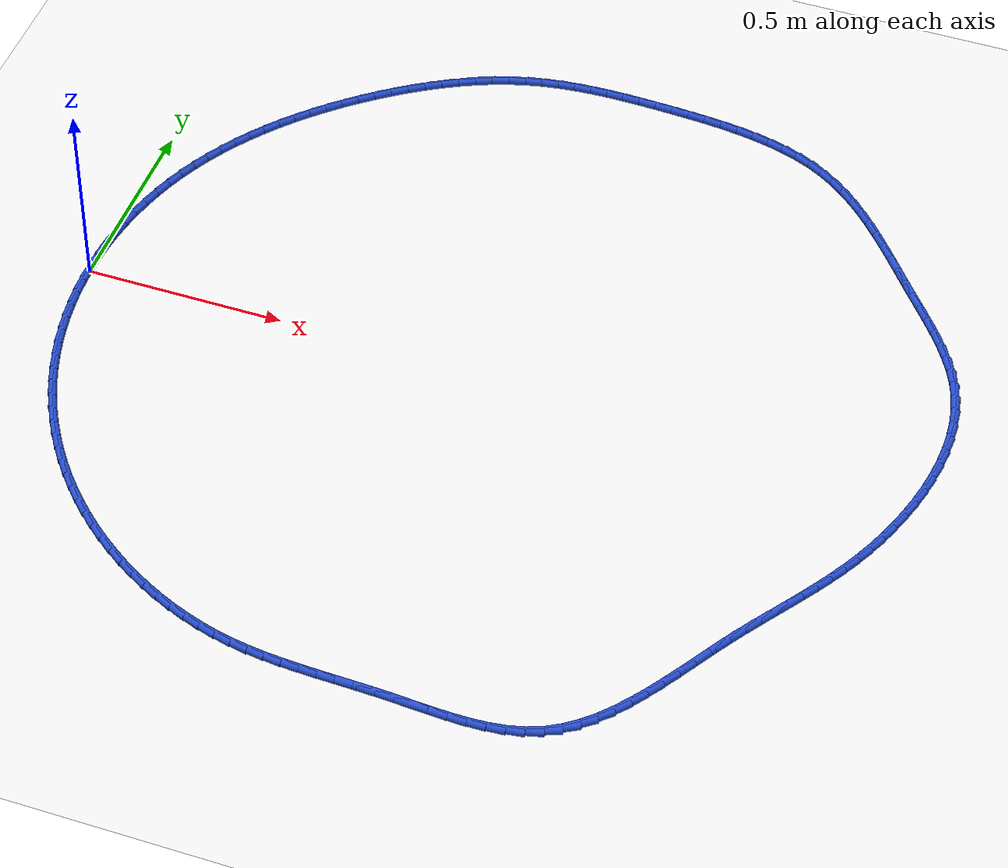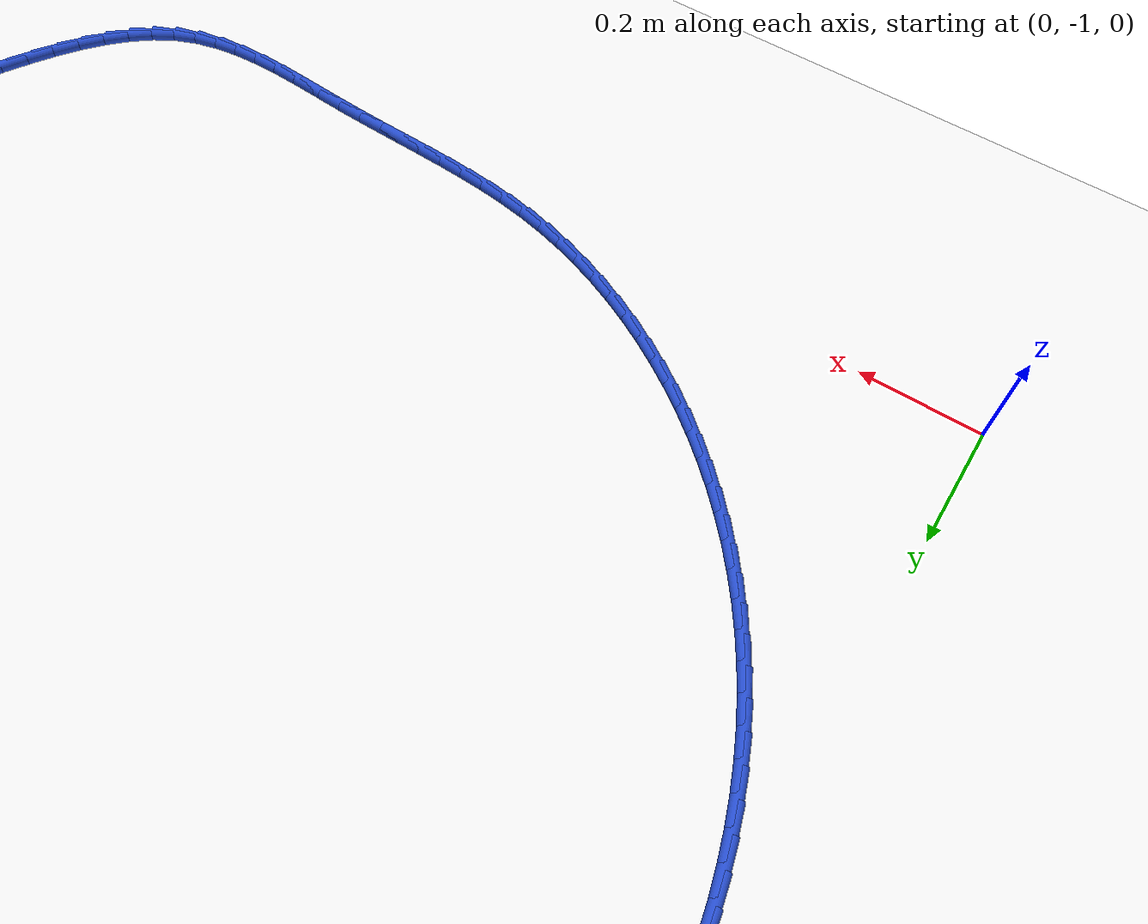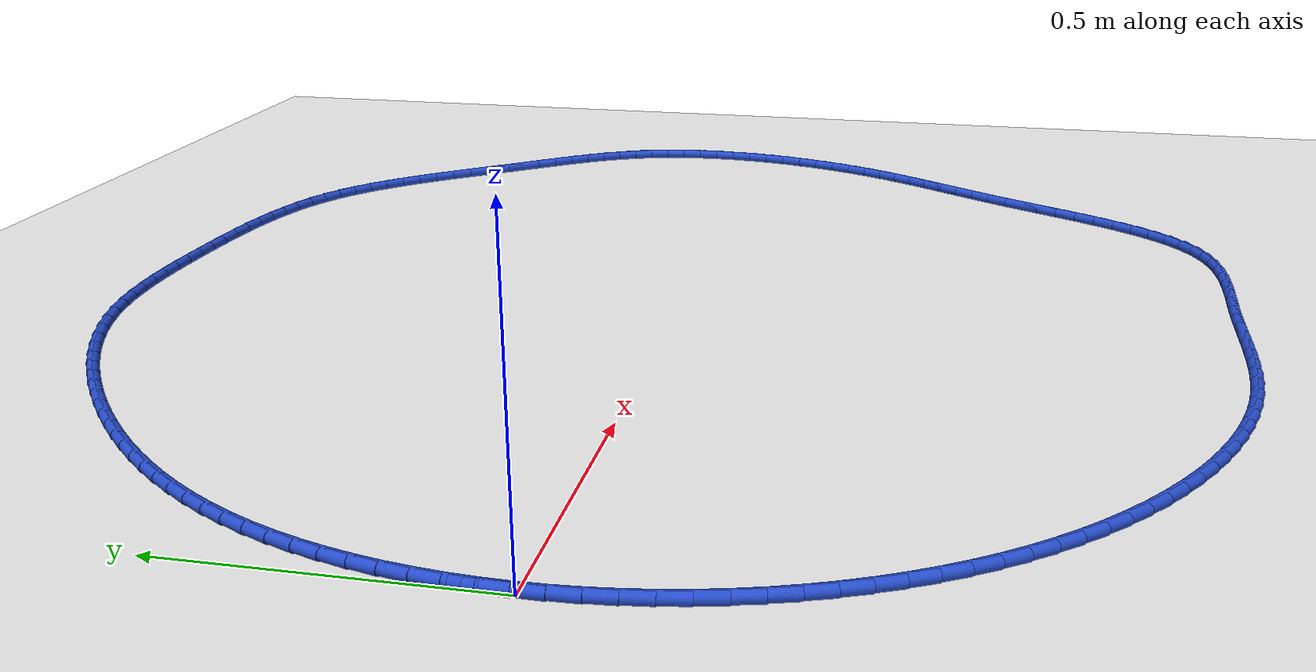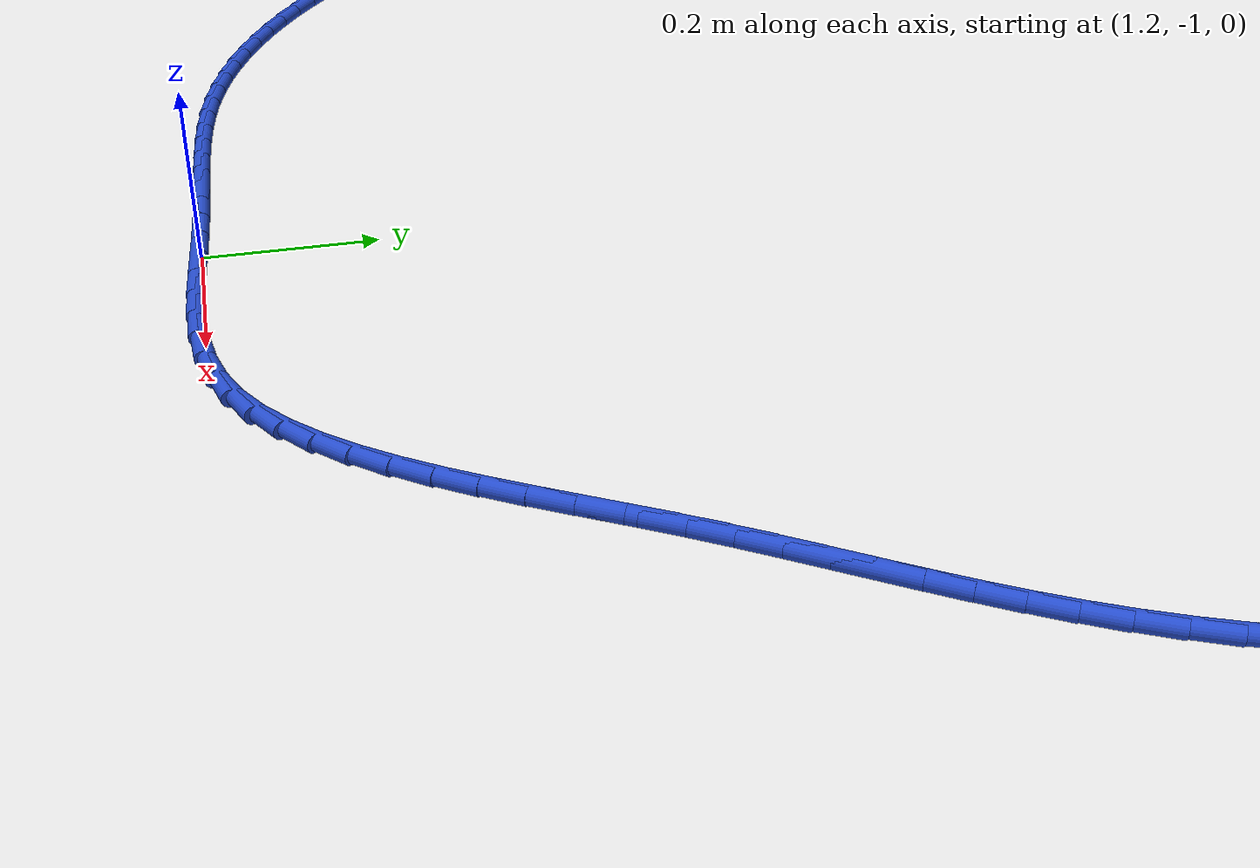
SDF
<sdf version="1.6">
 <world name="default">
  <light name="sun" type="directional">
   <pose>0 0 10 0 -0 0</pose>
   <diffuse>0.8 0.8 0.8 1</diffuse>
   <specular>0.2 0.2 0.2 1</specular>
   <attenuation>
    <range>1000</range>
    <constant>0.9</constant>
    <linear>0.01</linear>
    <quadratic>0.001</quadratic>
   </attenuation>
   <direction>-0.5 0.1 -0.9</direction>
  </light>
  <model name="ground_plane">
   <static>1</static>
   <link name="link">
    <collision name="collision">
     <geometry><plane><normal>0 0 1</normal><size>100 100</size></plane></geometry>
     <surface><friction><ode><mu>100</mu><mu2>50</mu2></ode></friction></surface>
    </collision>
    <visual name="visual">
     <cast_shadows>0</cast_shadows>
     <geometry><plane><normal>0 0 1</normal><size>100 100</size></plane></geometry>
     <material>
      <script><uri>file://media/materials/scripts/gazebo.material</uri><name>Gazebo/WhiteGlow</name></script>
     </material>
    </visual>
   </link>
  </model>
  <gravity>0 0 -9.8</gravity>
  <magnetic_field>6e-06 2.3e-05 -4.2e-05</magnetic_field>
  <atmosphere type="adiabatic"/>
  <physics name="default_physics" default="0" type="ode">
   <max_step_size>0.001</max_step_size>
   <real_time_factor>1</real_time_factor>
   <real_time_update_rate>1000</real_time_update_rate>
  </physics>
  <scene><ambient>0.4 0.4 0.4 1</ambient><background>0.7 0.7 0.7 1</background><shadows>1</shadows></scene>
  <spherical_coordinates>
   <surface_model>EARTH_WGS84</surface_model>
   <latitude_deg>0</latitude_deg>
   <longitude_deg>0</longitude_deg>
   <elevation>0</elevation>
   <heading_deg>0</heading_deg>
  </spherical_coordinates>
  <model name="line">
   <link name="link_0">
    <pose>1.0408340855860843e-17 -1.3877787807814457e-16 0.01 0 1.57 1.5510047050633564</pose>
    <collision name="collision">
     <geometry><cylinder><radius>0.01</radius><length>0.08</length></cylinder></geometry>
    </collision>
    <visual name="visual">
     <material>
      <script><name>Gazebo/Blue</name><uri>file://media/materials/scripts/gazebo.material</uri></script>
     </material>
     <geometry><cylinder><radius>0.01</radius><length>0.08</length></cylinder></geometry>
    </visual>
   </link>
   <link name="link_1">
    <pose>0.0008661670041303693 0.0437586125074585 0.01 0 1.57 1.5073824227022519</pose>
    <collision name="collision">
     <geometry><cylinder><radius>0.01</radius><length>0.08</length></cylinder></geometry>
    </collision>
    <visual name="visual">
     <material>
      <script><name>Gazebo/Blue</name><uri>file://media/materials/scripts/gazebo.material</uri></script>
     </material>
     <geometry><cylinder><radius>0.01</radius><length>0.08</length></cylinder></geometry>
    </visual>
   </link>
   <link name="link_2">
    <pose>0.003640453336723728 0.08744881905656593 0.01 0 1.57 1.4637581779412188</pose>
    <collision name="collision">
     <geometry><cylinder><radius>0.01</radius><length>0.08</length></cylinder></geometry>
    </collision>
    <visual name="visual">
     <material>
      <script><name>Gazebo/Blue</name><uri>file://media/materials/scripts/gazebo.material</uri></script>
     </material>
     <geometry><cylinder><radius>0.01</radius><length>0.08</length></cylinder></geometry>
    </visual>
   </link>
   <link name="link_3">
    <pose>0.00831672128322156 0.1309697077833986 0.01 0 1.57 1.4199958995333815</pose>
    <collision name="collision">
     <geometry><cylinder><radius>0.01</radius><length>0.08</length></cylinder></geometry>
    </collision>
    <visual name="visual">
     <material>
      <script><name>Gazebo/Blue</name><uri>file://media/materials/scripts/gazebo.material</uri></script>
     </material>
     <geometry><cylinder><radius>0.01</radius><length>0.08</length></cylinder></geometry>
    </visual>
   </link>
   <link name="link_4">
    <pose>0.014888833129065325 0.17422036682403302 0.01 0 1.57 1.3759603452155063</pose>
    <collision name="collision">
     <geometry><cylinder><radius>0.01</radius><length>0.08</length></cylinder></geometry>
    </collision>
    <visual name="visual">
     <material>
      <script><name>Gazebo/Blue</name><uri>file://media/materials/scripts/gazebo.material</uri></script>
     </material>
     <geometry><cylinder><radius>0.01</radius><length>0.08</length></cylinder></geometry>
    </visual>
   </link>
   <link name="link_5">
    <pose>0.023350651159696492 0.2170998843145456 0.01 0 1.57 1.3315179308007221</pose>
    <collision name="collision">
     <geometry><cylinder><radius>0.01</radius><length>0.08</length></cylinder></geometry>
    </collision>
    <visual name="visual">
     <material>
      <script><name>Gazebo/Blue</name><uri>file://media/materials/scripts/gazebo.material</uri></script>
     </material>
     <geometry><cylinder><radius>0.01</radius><length>0.08</length></cylinder></geometry>
    </visual>
   </link>
   <link name="link_6">
    <pose>0.033696037660556545 0.2595073483910131 0.01 0 1.57 1.286537709282582</pose>
    <collision name="collision">
     <geometry><cylinder><radius>0.01</radius><length>0.08</length></cylinder></geometry>
    </collision>
    <visual name="visual">
     <material>
      <script><name>Gazebo/Blue</name><uri>file://media/materials/scripts/gazebo.material</uri></script>
     </material>
     <geometry><cylinder><radius>0.01</radius><length>0.08</length></cylinder></geometry>
    </visual>
   </link>
   <link name="link_7">
    <pose>0.04591885491708693 0.30134184718951174 0.01 0 1.57 1.2408925728374436</pose>
    <collision name="collision">
     <geometry><cylinder><radius>0.01</radius><length>0.08</length></cylinder></geometry>
    </collision>
    <visual name="visual">
     <material>
      <script><name>Gazebo/Blue</name><uri>file://media/materials/scripts/gazebo.material</uri></script>
     </material>
     <geometry><cylinder><radius>0.01</radius><length>0.08</length></cylinder></geometry>
    </visual>
   </link>
   <link name="link_8">
    <pose>0.06001296521472912 0.3425024688461182 0.01 0 1.57 1.1944607478046259</pose>
    <collision name="collision">
     <geometry><cylinder><radius>0.01</radius><length>0.08</length></cylinder></geometry>
    </collision>
    <visual name="visual">
     <material>
      <script><name>Gazebo/Blue</name><uri>file://media/materials/scripts/gazebo.material</uri></script>
     </material>
     <geometry><cylinder><radius>0.01</radius><length>0.08</length></cylinder></geometry>
    </visual>
   </link>
   <link name="link_9">
    <pose>0.0759722308389246 0.38288830149690894 0.01 0 1.57 1.147153978568763</pose>
    <collision name="collision">
     <geometry><cylinder><radius>0.01</radius><length>0.08</length></cylinder></geometry>
    </collision>
    <visual name="visual">
     <material>
      <script><name>Gazebo/Blue</name><uri>file://media/materials/scripts/gazebo.material</uri></script>
     </material>
     <geometry><cylinder><radius>0.01</radius><length>0.08</length></cylinder></geometry>
    </visual>
   </link>
   <link name="link_10">
    <pose>0.09378972469658972 0.4223994590807371 0.01 0 1.57 1.0999242929448283</pose>
    <collision name="collision">
     <geometry><cylinder><radius>0.01</radius><length>0.08</length></cylinder></geometry>
    </collision>
    <visual name="visual">
     <material>
      <script><name>Gazebo/Blue</name><uri>file://media/materials/scripts/gazebo.material</uri></script>
     </material>
     <geometry><cylinder><radius>0.01</radius><length>0.08</length></cylinder></geometry>
    </visual>
   </link>
   <link name="link_11">
    <pose>0.11342769083888135 0.4609761178447701 0.01 0 1.57 1.0541549785975148</pose>
    <collision name="collision">
     <geometry><cylinder><radius>0.01</radius><length>0.08</length></cylinder></geometry>
    </collision>
    <visual name="visual">
     <material>
      <script><name>Gazebo/Blue</name><uri>file://media/materials/scripts/gazebo.material</uri></script>
     </material>
     <geometry><cylinder><radius>0.01</radius><length>0.08</length></cylinder></geometry>
    </visual>
   </link>
   <link name="link_12">
    <pose>0.13480824333574323 0.49861060322044926 0.01 0 1.57 1.00999541218974</pose>
    <collision name="collision">
     <geometry><cylinder><radius>0.01</radius><length>0.08</length></cylinder></geometry>
    </collision>
    <visual name="visual">
     <material>
      <script><name>Gazebo/Blue</name><uri>file://media/materials/scripts/gazebo.material</uri></script>
     </material>
     <geometry><cylinder><radius>0.01</radius><length>0.08</length></cylinder></geometry>
    </visual>
   </link>
   <link name="link_13">
    <pose>0.15785080601760312 0.5352987366238143 0.01 0 1.57 0.9674761682138244</pose>
    <collision name="collision">
     <geometry><cylinder><radius>0.01</radius><length>0.08</length></cylinder></geometry>
    </collision>
    <visual name="visual">
     <material>
      <script><name>Gazebo/Blue</name><uri>file://media/materials/scripts/gazebo.material</uri></script>
     </material>
     <geometry><cylinder><radius>0.01</radius><length>0.08</length></cylinder></geometry>
    </visual>
   </link>
   <link name="link_14">
    <pose>0.18247480271488886 0.5710363394709055 0.01 0 1.57 0.9266021937544706</pose>
    <collision name="collision">
     <geometry><cylinder><radius>0.01</radius><length>0.08</length></cylinder></geometry>
    </collision>
    <visual name="visual">
     <material>
      <script><name>Gazebo/Blue</name><uri>file://media/materials/scripts/gazebo.material</uri></script>
     </material>
     <geometry><cylinder><radius>0.01</radius><length>0.08</length></cylinder></geometry>
    </visual>
   </link>
   <link name="link_15">
    <pose>0.2085996572580282 0.605819233177763 0.01 0 1.57 0.8873565271350221</pose>
    <collision name="collision">
     <geometry><cylinder><radius>0.01</radius><length>0.08</length></cylinder></geometry>
    </collision>
    <visual name="visual">
     <material>
      <script><name>Gazebo/Blue</name><uri>file://media/materials/scripts/gazebo.material</uri></script>
     </material>
     <geometry><cylinder><radius>0.01</radius><length>0.08</length></cylinder></geometry>
    </visual>
   </link>
   <link name="link_16">
    <pose>0.23614479347744888 0.6396432391604265 0.01 0 1.57 0.8497040258405479</pose>
    <collision name="collision">
     <geometry><cylinder><radius>0.01</radius><length>0.08</length></cylinder></geometry>
    </collision>
    <visual name="visual">
     <material>
      <script><name>Gazebo/Blue</name><uri>file://media/materials/scripts/gazebo.material</uri></script>
     </material>
     <geometry><cylinder><radius>0.01</radius><length>0.08</length></cylinder></geometry>
    </visual>
   </link>
   <link name="link_17">
    <pose>0.2650296352035787 0.6725041788349362 0.01 0 1.57 0.8135949042184399</pose>
    <collision name="collision">
     <geometry><cylinder><radius>0.01</radius><length>0.08</length></cylinder></geometry>
    </collision>
    <visual name="visual">
     <material>
      <script><name>Gazebo/Blue</name><uri>file://media/materials/scripts/gazebo.material</uri></script>
     </material>
     <geometry><cylinder><radius>0.01</radius><length>0.08</length></cylinder></geometry>
    </visual>
   </link>
   <link name="link_18">
    <pose>0.29517360626684525 0.704397873617332 0.01 0 1.57 0.7789679485572772</pose>
    <collision name="collision">
     <geometry><cylinder><radius>0.01</radius><length>0.08</length></cylinder></geometry>
    </collision>
    <visual name="visual">
     <material>
      <script><name>Gazebo/Blue</name><uri>file://media/materials/scripts/gazebo.material</uri></script>
     </material>
     <geometry><cylinder><radius>0.01</radius><length>0.08</length></cylinder></geometry>
    </visual>
   </link>
   <link name="link_19">
    <pose>0.3264961304976766 0.735320144923654 0.01 0 1.57 0.7457533346031334</pose>
    <collision name="collision">
     <geometry><cylinder><radius>0.01</radius><length>0.08</length></cylinder></geometry>
    </collision>
    <visual name="visual">
     <material>
      <script><name>Gazebo/Blue</name><uri>file://media/materials/scripts/gazebo.material</uri></script>
     </material>
     <geometry><cylinder><radius>0.01</radius><length>0.08</length></cylinder></geometry>
    </visual>
   </link>
   <link name="link_20">
    <pose>0.3589166317265001 0.7652668141699421 0.01 0 1.57 0.7138750176041784</pose>
    <collision name="collision">
     <geometry><cylinder><radius>0.01</radius><length>0.08</length></cylinder></geometry>
    </collision>
    <visual name="visual">
     <material>
      <script><name>Gazebo/Blue</name><uri>file://media/materials/scripts/gazebo.material</uri></script>
     </material>
     <geometry><cylinder><radius>0.01</radius><length>0.08</length></cylinder></geometry>
    </visual>
   </link>
   <link name="link_21">
    <pose>0.39235453378374396 0.7942337027722364 0.01 0 1.57 0.6832103914307424</pose>
    <collision name="collision">
     <geometry><cylinder><radius>0.01</radius><length>0.08</length></cylinder></geometry>
    </collision>
    <visual name="visual">
     <material>
      <script><name>Gazebo/Blue</name><uri>file://media/materials/scripts/gazebo.material</uri></script>
     </material>
     <geometry><cylinder><radius>0.01</radius><length>0.08</length></cylinder></geometry>
    </visual>
   </link>
   <link name="link_22">
    <pose>0.4267297880257817 0.8222146436564644 0.01 0 1.57 0.6521258205594856</pose>
    <collision name="collision">
     <geometry><cylinder><radius>0.01</radius><length>0.08</length></cylinder></geometry>
    </collision>
    <visual name="visual">
     <material>
      <script><name>Gazebo/Blue</name><uri>file://media/materials/scripts/gazebo.material</uri></script>
     </material>
     <geometry><cylinder><radius>0.01</radius><length>0.08</length></cylinder></geometry>
    </visual>
   </link>
   <link name="link_23">
    <pose>0.46198142945039494 0.8491315346474649 0.01 0 1.57 0.6185035362746216</pose>
    <collision name="collision">
     <geometry><cylinder><radius>0.01</radius><length>0.08</length></cylinder></geometry>
    </collision>
    <visual name="visual">
     <material>
      <script><name>Gazebo/Blue</name><uri>file://media/materials/scripts/gazebo.material</uri></script>
     </material>
     <geometry><cylinder><radius>0.01</radius><length>0.08</length></cylinder></geometry>
    </visual>
   </link>
   <link name="link_24">
    <pose>0.49807248970099144 0.8748158190759854 0.01 0 1.57 0.5819867778900134</pose>
    <collision name="collision">
     <geometry><cylinder><radius>0.01</radius><length>0.08</length></cylinder></geometry>
    </collision>
    <visual name="visual">
     <material>
      <script><name>Gazebo/Blue</name><uri>file://media/materials/scripts/gazebo.material</uri></script>
     </material>
     <geometry><cylinder><radius>0.01</radius><length>0.08</length></cylinder></geometry>
    </visual>
   </link>
   <link name="link_25">
    <pose>0.5349675267407503 0.8990931868652021 0.01 0 1.57 0.5423304885213913</pose>
    <collision name="collision">
     <geometry><cylinder><radius>0.01</radius><length>0.08</length></cylinder></geometry>
    </collision>
    <visual name="visual">
     <material>
      <script><name>Gazebo/Blue</name><uri>file://media/materials/scripts/gazebo.material</uri></script>
     </material>
     <geometry><cylinder><radius>0.01</radius><length>0.08</length></cylinder></geometry>
    </visual>
   </link>
   <link name="link_26">
    <pose>0.5726310985328501 0.9217893279382899 0.01 0 1.57 0.49928588309935407</pose>
    <collision name="collision">
     <geometry><cylinder><radius>0.01</radius><length>0.08</length></cylinder></geometry>
    </collision>
    <visual name="visual">
     <material>
      <script><name>Gazebo/Blue</name><uri>file://media/materials/scripts/gazebo.material</uri></script>
     </material>
     <geometry><cylinder><radius>0.01</radius><length>0.08</length></cylinder></geometry>
    </visual>
   </link>
   <link name="link_27">
    <pose>0.6110277630404698 0.9427299322184245 0.01 0 1.57 0.452610946824274</pose>
    <collision name="collision">
     <geometry><cylinder><radius>0.01</radius><length>0.08</length></cylinder></geometry>
    </collision>
    <visual name="visual">
     <material>
      <script><name>Gazebo/Blue</name><uri>file://media/materials/scripts/gazebo.material</uri></script>
     </material>
     <geometry><cylinder><radius>0.01</radius><length>0.08</length></cylinder></geometry>
    </visual>
   </link>
   <link name="link_28">
    <pose>0.6501220782267878 0.9617406896287812 0.01 0 1.57 0.4020853352109531</pose>
    <collision name="collision">
     <geometry><cylinder><radius>0.01</radius><length>0.08</length></cylinder></geometry>
    </collision>
    <visual name="visual">
     <material>
      <script><name>Gazebo/Blue</name><uri>file://media/materials/scripts/gazebo.material</uri></script>
     </material>
     <geometry><cylinder><radius>0.01</radius><length>0.08</length></cylinder></geometry>
    </visual>
   </link>
   <link name="link_29">
    <pose>0.689878602054983 0.9786472900925355 0.01 0 1.57 0.3475303870564808</pose>
    <collision name="collision">
     <geometry><cylinder><radius>0.01</radius><length>0.08</length></cylinder></geometry>
    </collision>
    <visual name="visual">
     <material>
      <script><name>Gazebo/Blue</name><uri>file://media/materials/scripts/gazebo.material</uri></script>
     </material>
     <geometry><cylinder><radius>0.01</radius><length>0.08</length></cylinder></geometry>
    </visual>
   </link>
   <link name="link_30">
    <pose>0.7302618924882339 0.9932754235328627 0.01 0 1.57 0.2888344512729044</pose>
    <collision name="collision">
     <geometry><cylinder><radius>0.01</radius><length>0.08</length></cylinder></geometry>
    </collision>
    <visual name="visual">
     <material>
      <script><name>Gazebo/Blue</name><uri>file://media/materials/scripts/gazebo.material</uri></script>
     </material>
     <geometry><cylinder><radius>0.01</radius><length>0.08</length></cylinder></geometry>
    </visual>
   </link>
   <link name="link_31">
    <pose>0.7712365074897194 1.005450779872938 0.01 0 1.57 0.22665506433912064</pose>
    <collision name="collision">
     <geometry><cylinder><radius>0.01</radius><length>0.08</length></cylinder></geometry>
    </collision>
    <visual name="visual">
     <material>
      <script><name>Gazebo/Blue</name><uri>file://media/materials/scripts/gazebo.material</uri></script>
     </material>
     <geometry><cylinder><radius>0.01</radius><length>0.08</length></cylinder></geometry>
    </visual>
   </link>
   <link name="link_32">
    <pose>0.8127670217429207 1.0150284554934534 0.01 0 1.57 0.16758040289350418</pose>
    <collision name="collision">
     <geometry><cylinder><radius>0.01</radius><length>0.08</length></cylinder></geometry>
    </collision>
    <visual name="visual">
     <material>
      <script><name>Gazebo/Blue</name><uri>file://media/materials/scripts/gazebo.material</uri></script>
     </material>
     <geometry><cylinder><radius>0.01</radius><length>0.08</length></cylinder></geometry>
    </visual>
   </link>
   <link name="link_33">
    <pose>0.8548181683261065 1.0221421200556822 0.01 0 1.57 0.11554661833901113</pose>
    <collision name="collision">
     <geometry><cylinder><radius>0.01</radius><length>0.08</length></cylinder></geometry>
    </collision>
    <visual name="visual">
     <material>
      <script><name>Gazebo/Blue</name><uri>file://media/materials/scripts/gazebo.material</uri></script>
     </material>
     <geometry><cylinder><radius>0.01</radius><length>0.08</length></cylinder></geometry>
    </visual>
   </link>
   <link name="link_34">
    <pose>0.8973547676691845 1.0270790709578395 0.01 0 1.57 0.07081333367064521</pose>
    <collision name="collision">
     <geometry><cylinder><radius>0.01</radius><length>0.08</length></cylinder></geometry>
    </collision>
    <visual name="visual">
     <material>
      <script><name>Gazebo/Blue</name><uri>file://media/materials/scripts/gazebo.material</uri></script>
     </material>
     <geometry><cylinder><radius>0.01</radius><length>0.08</length></cylinder></geometry>
    </visual>
   </link>
   <link name="link_35">
    <pose>0.9403416411161021 1.0301282131451883 0.01 0 1.57 0.03340168854281028</pose>
    <collision name="collision">
     <geometry><cylinder><radius>0.01</radius><length>0.08</length></cylinder></geometry>
    </collision>
    <visual name="visual">
     <material>
      <script><name>Gazebo/Blue</name><uri>file://media/materials/scripts/gazebo.material</uri></script>
     </material>
     <geometry><cylinder><radius>0.01</radius><length>0.08</length></cylinder></geometry>
    </visual>
   </link>
   <link name="link_36">
    <pose>0.9837436100108066 1.0315784515629902 0.01 0 1.57 0.003203130968377201</pose>
    <collision name="collision">
     <geometry><cylinder><radius>0.01</radius><length>0.08</length></cylinder></geometry>
    </collision>
    <visual name="visual">
     <material>
      <script><name>Gazebo/Blue</name><uri>file://media/materials/scripts/gazebo.material</uri></script>
     </material>
     <geometry><cylinder><radius>0.01</radius><length>0.08</length></cylinder></geometry>
    </visual>
   </link>
   <link name="link_37">
    <pose>1.0275254956972457 1.0317186911565084 0.01 0 1.57 -0.01995931789442275</pose>
    <collision name="collision">
     <geometry><cylinder><radius>0.01</radius><length>0.08</length></cylinder></geometry>
    </collision>
    <visual name="visual">
     <material>
      <script><name>Gazebo/Blue</name><uri>file://media/materials/scripts/gazebo.material</uri></script>
     </material>
     <geometry><cylinder><radius>0.01</radius><length>0.08</length></cylinder></geometry>
    </visual>
   </link>
   <link name="link_38">
    <pose>1.071652119519367 1.0308378368710045 0.01 0 1.57 -0.036284288018105695</pose>
    <collision name="collision">
     <geometry><cylinder><radius>0.01</radius><length>0.08</length></cylinder></geometry>
    </collision>
    <visual name="visual">
     <material>
      <script><name>Gazebo/Blue</name><uri>file://media/materials/scripts/gazebo.material</uri></script>
     </material>
     <geometry><cylinder><radius>0.01</radius><length>0.08</length></cylinder></geometry>
    </visual>
   </link>
   <link name="link_39">
    <pose>1.1160883028211177 1.0292247936517411 0.01 0 1.57 -0.04643816507529963</pose>
    <collision name="collision">
     <geometry><cylinder><radius>0.01</radius><length>0.08</length></cylinder></geometry>
    </collision>
    <visual name="visual">
     <material>
      <script><name>Gazebo/Blue</name><uri>file://media/materials/scripts/gazebo.material</uri></script>
     </material>
     <geometry><cylinder><radius>0.01</radius><length>0.08</length></cylinder></geometry>
    </visual>
   </link>
   <link name="link_40">
    <pose>1.160792513021975 1.0271473185836058 0.01 0 1.57 -0.057548799111874716</pose>
    <collision name="collision">
     <geometry><cylinder><radius>0.01</radius><length>0.08</length></cylinder></geometry>
    </collision>
    <visual name="visual">
     <material>
      <script><name>Gazebo/Blue</name><uri>file://media/materials/scripts/gazebo.material</uri></script>
     </material>
     <geometry><cylinder><radius>0.01</radius><length>0.08</length></cylinder></geometry>
    </visual>
   </link>
   <link name="link_41">
    <pose>1.2056303577323875 1.024564102081764 0.01 0 1.57 -0.07501468954205713</pose>
    <collision name="collision">
     <geometry><cylinder><radius>0.01</radius><length>0.08</length></cylinder></geometry>
    </collision>
    <visual name="visual">
     <material>
      <script><name>Gazebo/Blue</name><uri>file://media/materials/scripts/gazebo.material</uri></script>
     </material>
     <geometry><cylinder><radius>0.01</radius><length>0.08</length></cylinder></geometry>
    </visual>
   </link>
   <link name="link_42">
    <pose>1.2503970764528456 1.0211996273448591 0.01 0 1.57 -0.09918247661691425</pose>
    <collision name="collision">
     <geometry><cylinder><radius>0.01</radius><length>0.08</length></cylinder></geometry>
    </collision>
    <visual name="visual">
     <material>
      <script><name>Gazebo/Blue</name><uri>file://media/materials/scripts/gazebo.material</uri></script>
     </material>
     <geometry><cylinder><radius>0.01</radius><length>0.08</length></cylinder></geometry>
    </visual>
   </link>
   <link name="link_43">
    <pose>1.2948861618503702 1.016772563559976 0.01 0 1.57 -0.13039980829297934</pose>
    <collision name="collision">
     <geometry><cylinder><radius>0.01</radius><length>0.08</length></cylinder></geometry>
    </collision>
    <visual name="visual">
     <material>
      <script><name>Gazebo/Blue</name><uri>file://media/materials/scripts/gazebo.material</uri></script>
     </material>
     <geometry><cylinder><radius>0.01</radius><length>0.08</length></cylinder></geometry>
    </visual>
   </link>
   <link name="link_44">
    <pose>1.3388911065919833 1.0110015799141998 0.01 0 1.57 -0.16912613754877995</pose>
    <collision name="collision">
     <geometry><cylinder><radius>0.01</radius><length>0.08</length></cylinder></geometry>
    </collision>
    <visual name="visual">
     <material>
      <script><name>Gazebo/Blue</name><uri>file://media/materials/scripts/gazebo.material</uri></script>
     </material>
     <geometry><cylinder><radius>0.01</radius><length>0.08</length></cylinder></geometry>
    </visual>
   </link>
   <link name="link_45">
    <pose>1.3822054033447055 1.0036053455946148 0.01 0 1.57 -0.21589909365717055</pose>
    <collision name="collision">
     <geometry><cylinder><radius>0.01</radius><length>0.08</length></cylinder></geometry>
    </collision>
    <visual name="visual">
     <material>
      <script><name>Gazebo/Blue</name><uri>file://media/materials/scripts/gazebo.material</uri></script>
     </material>
     <geometry><cylinder><radius>0.01</radius><length>0.08</length></cylinder></geometry>
    </visual>
   </link>
   <link name="link_46">
    <pose>1.4246225447755565 0.9943025297883058 0.01 0 1.57 -0.2712785358437303</pose>
    <collision name="collision">
     <geometry><cylinder><radius>0.01</radius><length>0.08</length></cylinder></geometry>
    </collision>
    <visual name="visual">
     <material>
      <script><name>Gazebo/Blue</name><uri>file://media/materials/scripts/gazebo.material</uri></script>
     </material>
     <geometry><cylinder><radius>0.01</radius><length>0.08</length></cylinder></geometry>
    </visual>
   </link>
   <link name="link_47">
    <pose>1.4659360235515593 0.982811801682358 0.01 0 1.57 -0.33575729902039086</pose>
    <collision name="collision">
     <geometry><cylinder><radius>0.01</radius><length>0.08</length></cylinder></geometry>
    </collision>
    <visual name="visual">
     <material>
      <script><name>Gazebo/Blue</name><uri>file://media/materials/scripts/gazebo.material</uri></script>
     </material>
     <geometry><cylinder><radius>0.01</radius><length>0.08</length></cylinder></geometry>
    </visual>
   </link>
   <link name="link_48">
    <pose>1.5059393323397339 0.9688518304638558 0.01 0 1.57 -0.4096295952911585</pose>
    <collision name="collision">
     <geometry><cylinder><radius>0.01</radius><length>0.08</length></cylinder></geometry>
    </collision>
    <visual name="visual">
     <material>
      <script><name>Gazebo/Blue</name><uri>file://media/materials/scripts/gazebo.material</uri></script>
     </material>
     <geometry><cylinder><radius>0.01</radius><length>0.08</length></cylinder></geometry>
    </visual>
   </link>
   <link name="link_49">
    <pose>1.5444259638071016 0.9521412853198846 0.01 0 1.57 -0.4925403948413887</pose>
    <collision name="collision">
     <geometry><cylinder><radius>0.01</radius><length>0.08</length></cylinder></geometry>
    </collision>
    <visual name="visual">
     <material>
      <script><name>Gazebo/Blue</name><uri>file://media/materials/scripts/gazebo.material</uri></script>
     </material>
     <geometry><cylinder><radius>0.01</radius><length>0.08</length></cylinder></geometry>
    </visual>
   </link>
   <link name="link_50">
    <pose>1.5811957664802025 0.9324085601762867 0.01 0 1.57 -0.575983143911066</pose>
    <collision name="collision">
     <geometry><cylinder><radius>0.01</radius><length>0.08</length></cylinder></geometry>
    </collision>
    <visual name="visual">
     <material>
      <script><name>Gazebo/Blue</name><uri>file://media/materials/scripts/gazebo.material</uri></script>
     </material>
     <geometry><cylinder><radius>0.01</radius><length>0.08</length></cylinder></geometry>
    </visual>
   </link>
   <link name="link_51">
    <pose>1.6162282689702971 0.9096569672258691 0.01 0 1.57 -0.6502326067444143</pose>
    <collision name="collision">
     <geometry><cylinder><radius>0.01</radius><length>0.08</length></cylinder></geometry>
    </collision>
    <visual name="visual">
     <material>
      <script><name>Gazebo/Blue</name><uri>file://media/materials/scripts/gazebo.material</uri></script>
     </material>
     <geometry><cylinder><radius>0.01</radius><length>0.08</length></cylinder></geometry>
    </visual>
   </link>
   <link name="link_52">
    <pose>1.6497035297703901 0.884196638015675 0.01 0 1.57 -0.7143633719763558</pose>
    <collision name="collision">
     <geometry><cylinder><radius>0.01</radius><length>0.08</length></cylinder></geometry>
    </collision>
    <visual name="visual">
     <material>
      <script><name>Gazebo/Blue</name><uri>file://media/materials/scripts/gazebo.material</uri></script>
     </material>
     <geometry><cylinder><radius>0.01</radius><length>0.08</length></cylinder></geometry>
    </visual>
   </link>
   <link name="link_53">
    <pose>1.6818121489541316 0.8563538331650749 0.01 0 1.57 -0.7684093224931483</pose>
    <collision name="collision">
     <geometry><cylinder><radius>0.01</radius><length>0.08</length></cylinder></geometry>
    </collision>
    <visual name="visual">
     <material>
      <script><name>Gazebo/Blue</name><uri>file://media/materials/scripts/gazebo.material</uri></script>
     </material>
     <geometry><cylinder><radius>0.01</radius><length>0.08</length></cylinder></geometry>
    </visual>
   </link>
   <link name="link_54">
    <pose>1.7127447265951725 0.8264548132934387 0.01 0 1.57 -0.8127045335842418</pose>
    <collision name="collision">
     <geometry><cylinder><radius>0.01</radius><length>0.08</length></cylinder></geometry>
    </collision>
    <visual name="visual">
     <material>
      <script><name>Gazebo/Blue</name><uri>file://media/materials/scripts/gazebo.material</uri></script>
     </material>
     <geometry><cylinder><radius>0.01</radius><length>0.08</length></cylinder></geometry>
    </visual>
   </link>
   <link name="link_55">
    <pose>1.7426918627671621 0.7948258390201363 0.01 0 1.57 -0.8477178680415633</pose>
    <collision name="collision">
     <geometry><cylinder><radius>0.01</radius><length>0.08</length></cylinder></geometry>
    </collision>
    <visual name="visual">
     <material>
      <script><name>Gazebo/Blue</name><uri>file://media/materials/scripts/gazebo.material</uri></script>
     </material>
     <geometry><cylinder><radius>0.01</radius><length>0.08</length></cylinder></geometry>
    </visual>
   </link>
   <link name="link_56">
    <pose>1.7718441575437502 0.7617931709645375 0.01 0 1.57 -0.8739342403804962</pose>
    <collision name="collision">
     <geometry><cylinder><radius>0.01</radius><length>0.08</length></cylinder></geometry>
    </collision>
    <visual name="visual">
     <material>
      <script><name>Gazebo/Blue</name><uri>file://media/materials/scripts/gazebo.material</uri></script>
     </material>
     <geometry><cylinder><radius>0.01</radius><length>0.08</length></cylinder></geometry>
    </visual>
   </link>
   <link name="link_57">
    <pose>1.8003922109985881 0.7276830697460126 0.01 0 1.57 -0.8917779430810567</pose>
    <collision name="collision">
     <geometry><cylinder><radius>0.01</radius><length>0.08</length></cylinder></geometry>
    </collision>
    <visual name="visual">
     <material>
      <script><name>Gazebo/Blue</name><uri>file://media/materials/scripts/gazebo.material</uri></script>
     </material>
     <geometry><cylinder><radius>0.01</radius><length>0.08</length></cylinder></geometry>
    </visual>
   </link>
   <link name="link_58">
    <pose>1.8285266232053246 0.6928217959839309 0.01 0 1.57 -0.901567364842364</pose>
    <collision name="collision">
     <geometry><cylinder><radius>0.01</radius><length>0.08</length></cylinder></geometry>
    </collision>
    <visual name="visual">
     <material>
      <script><name>Gazebo/Blue</name><uri>file://media/materials/scripts/gazebo.material</uri></script>
     </material>
     <geometry><cylinder><radius>0.01</radius><length>0.08</length></cylinder></geometry>
    </visual>
   </link>
   <link name="link_59">
    <pose>1.8564379942376108 0.657535610297663 0.01 0 1.57 -0.9034907593197451</pose>
    <collision name="collision">
     <geometry><cylinder><radius>0.01</radius><length>0.08</length></cylinder></geometry>
    </collision>
    <visual name="visual">
     <material>
      <script><name>Gazebo/Blue</name><uri>file://media/materials/scripts/gazebo.material</uri></script>
     </material>
     <geometry><cylinder><radius>0.01</radius><length>0.08</length></cylinder></geometry>
    </visual>
   </link>
   <link name="link_60">
    <pose>1.8843169241690954 0.6221507733065785 0.01 0 1.57 -0.8978523942312365</pose>
    <collision name="collision">
     <geometry><cylinder><radius>0.01</radius><length>0.08</length></cylinder></geometry>
    </collision>
    <visual name="visual">
     <material>
      <script><name>Gazebo/Blue</name><uri>file://media/materials/scripts/gazebo.material</uri></script>
     </material>
     <geometry><cylinder><radius>0.01</radius><length>0.08</length></cylinder></geometry>
    </visual>
   </link>
   <link name="link_61">
    <pose>1.9123451348355691 0.5869861539180188 0.01 0 1.57 -0.8932476660833276</pose>
    <collision name="collision">
     <geometry><cylinder><radius>0.01</radius><length>0.08</length></cylinder></geometry>
    </collision>
    <visual name="visual">
     <material>
      <script><name>Gazebo/Blue</name><uri>file://media/materials/scripts/gazebo.material</uri></script>
     </material>
     <geometry><cylinder><radius>0.01</radius><length>0.08</length></cylinder></geometry>
    </visual>
   </link>
   <link name="link_62">
    <pose>1.9404055334865529 0.5521118384085393 0.01 0 1.57 -0.9002894460323223</pose>
    <collision name="collision">
     <geometry><cylinder><radius>0.01</radius><length>0.08</length></cylinder></geometry>
    </collision>
    <visual name="visual">
     <material>
      <script><name>Gazebo/Blue</name><uri>file://media/materials/scripts/gazebo.material</uri></script>
     </material>
     <geometry><cylinder><radius>0.01</radius><length>0.08</length></cylinder></geometry>
    </visual>
   </link>
   <link name="link_63">
    <pose>1.9680177139076493 0.5172954309018589 0.01 0 1.57 -0.9199368609467999</pose>
    <collision name="collision">
     <geometry><cylinder><radius>0.01</radius><length>0.08</length></cylinder></geometry>
    </collision>
    <visual name="visual">
     <material>
      <script><name>Gazebo/Blue</name><uri>file://media/materials/scripts/gazebo.material</uri></script>
     </material>
     <geometry><cylinder><radius>0.01</radius><length>0.08</length></cylinder></geometry>
    </visual>
   </link>
   <link name="link_64">
    <pose>1.9946793372104046 0.4822862751401676 0.01 0 1.57 -0.9526892360861768</pose>
    <collision name="collision">
     <geometry><cylinder><radius>0.01</radius><length>0.08</length></cylinder></geometry>
    </collision>
    <visual name="visual">
     <material>
      <script><name>Gazebo/Blue</name><uri>file://media/materials/scripts/gazebo.material</uri></script>
     </material>
     <geometry><cylinder><radius>0.01</radius><length>0.08</length></cylinder></geometry>
    </visual>
   </link>
   <link name="link_65">
    <pose>2.019888064506368 0.4468337148656561 0.01 0 1.57 -0.9991382915906856</pose>
    <collision name="collision">
     <geometry><cylinder><radius>0.01</radius><length>0.08</length></cylinder></geometry>
    </collision>
    <visual name="visual">
     <material>
      <script><name>Gazebo/Blue</name><uri>file://media/materials/scripts/gazebo.material</uri></script>
     </material>
     <geometry><cylinder><radius>0.01</radius><length>0.08</length></cylinder></geometry>
    </visual>
   </link>
   <link name="link_66">
    <pose>2.0431415569070865 0.4106870938205144 0.01 0 1.57 -1.0597997818237335</pose>
    <collision name="collision">
     <geometry><cylinder><radius>0.01</radius><length>0.08</length></cylinder></geometry>
    </collision>
    <visual name="visual">
     <material>
      <script><name>Gazebo/Blue</name><uri>file://media/materials/scripts/gazebo.material</uri></script>
     </material>
     <geometry><cylinder><radius>0.01</radius><length>0.08</length></cylinder></geometry>
    </visual>
   </link>
   <link name="link_67">
    <pose>2.063937475524108 0.3735957557469327 0.01 0 1.57 -1.1348369613963785</pose>
    <collision name="collision">
     <geometry><cylinder><radius>0.01</radius><length>0.08</length></cylinder></geometry>
    </collision>
    <visual name="visual">
     <material>
      <script><name>Gazebo/Blue</name><uri>file://media/materials/scripts/gazebo.material</uri></script>
     </material>
     <geometry><cylinder><radius>0.01</radius><length>0.08</length></cylinder></geometry>
    </visual>
   </link>
   <link name="link_68">
    <pose>2.08177348146898 0.3353090443871021 0.01 0 1.57 -1.2230090784741638</pose>
    <collision name="collision">
     <geometry><cylinder><radius>0.01</radius><length>0.08</length></cylinder></geometry>
    </collision>
    <visual name="visual">
     <material>
      <script><name>Gazebo/Blue</name><uri>file://media/materials/scripts/gazebo.material</uri></script>
     </material>
     <geometry><cylinder><radius>0.01</radius><length>0.08</length></cylinder></geometry>
    </visual>
   </link>
   <link name="link_69">
    <pose>2.096171289173053 0.2955934656160376 0.01 0 1.57 -1.3129834698212568</pose>
    <collision name="collision">
     <geometry><cylinder><radius>0.01</radius><length>0.08</length></cylinder></geometry>
    </collision>
    <visual name="visual">
     <material>
      <script><name>Gazebo/Blue</name><uri>file://media/materials/scripts/gazebo.material</uri></script>
     </material>
     <geometry><cylinder><radius>0.01</radius><length>0.08</length></cylinder></geometry>
    </visual>
   </link>
   <link name="link_70">
    <pose>2.1070138944297727 0.25447330089958536 0.01 0 1.57 -1.3964854335596224</pose>
    <collision name="collision">
     <geometry><cylinder><radius>0.01</radius><length>0.08</length></cylinder></geometry>
    </collision>
    <visual name="visual">
     <material>
      <script><name>Gazebo/Blue</name><uri>file://media/materials/scripts/gazebo.material</uri></script>
     </material>
     <geometry><cylinder><radius>0.01</radius><length>0.08</length></cylinder></geometry>
    </visual>
   </link>
   <link name="link_71">
    <pose>2.114463111742006 0.21217176988611572 0.01 0 1.57 -1.4734308564868273</pose>
    <collision name="collision">
     <geometry><cylinder><radius>0.01</radius><length>0.08</length></cylinder></geometry>
    </collision>
    <visual name="visual">
     <material>
      <script><name>Gazebo/Blue</name><uri>file://media/materials/scripts/gazebo.material</uri></script>
     </material>
     <geometry><cylinder><radius>0.01</radius><length>0.08</length></cylinder></geometry>
    </visual>
   </link>
   <link name="link_72">
    <pose>2.118687968556996 0.16891723868654537 0.01 0 1.57 -1.5442099150164257</pose>
    <collision name="collision">
     <geometry><cylinder><radius>0.01</radius><length>0.08</length></cylinder></geometry>
    </collision>
    <visual name="visual">
     <material>
      <script><name>Gazebo/Blue</name><uri>file://media/materials/scripts/gazebo.material</uri></script>
     </material>
     <geometry><cylinder><radius>0.01</radius><length>0.08</length></cylinder></geometry>
    </visual>
   </link>
   <link name="link_73">
    <pose>2.1198574923219864 0.12493807341178978 0.01 0 1.57 1.532214804391361</pose>
    <collision name="collision">
     <geometry><cylinder><radius>0.01</radius><length>0.08</length></cylinder></geometry>
    </collision>
    <visual name="visual">
     <material>
      <script><name>Gazebo/Blue</name><uri>file://media/materials/scripts/gazebo.material</uri></script>
     </material>
     <geometry><cylinder><radius>0.01</radius><length>0.08</length></cylinder></geometry>
    </visual>
   </link>
   <link name="link_74">
    <pose>2.1181407104842194 0.08046264017276486 0.01 0 1.57 1.4720189425014627</pose>
    <collision name="collision">
     <geometry><cylinder><radius>0.01</radius><length>0.08</length></cylinder></geometry>
    </collision>
    <visual name="visual">
     <material>
      <script><name>Gazebo/Blue</name><uri>file://media/materials/scripts/gazebo.material</uri></script>
     </material>
     <geometry><cylinder><radius>0.01</radius><length>0.08</length></cylinder></geometry>
    </visual>
   </link>
   <link name="link_75">
    <pose>2.1137066504909394 0.03571930508038645 0.01 0 1.57 1.4161268489571401</pose>
    <collision name="collision">
     <geometry><cylinder><radius>0.01</radius><length>0.08</length></cylinder></geometry>
    </collision>
    <visual name="visual">
     <material>
      <script><name>Gazebo/Blue</name><uri>file://media/materials/scripts/gazebo.material</uri></script>
     </material>
     <geometry><cylinder><radius>0.01</radius><length>0.08</length></cylinder></geometry>
    </visual>
   </link>
   <link name="link_76">
    <pose>2.1067243397893876 -0.009063565754429945 0.01 0 1.57 1.3638731733381728</pose>
    <collision name="collision">
     <geometry><cylinder><radius>0.01</radius><length>0.08</length></cylinder></geometry>
    </collision>
    <visual name="visual">
     <material>
      <script><name>Gazebo/Blue</name><uri>file://media/materials/scripts/gazebo.material</uri></script>
     </material>
     <geometry><cylinder><radius>0.01</radius><length>0.08</length></cylinder></geometry>
    </visual>
   </link>
   <link name="link_77">
    <pose>2.0973628058268092 -0.05365760622076811 0.01 0 1.57 1.314610967232729</pose>
    <collision name="collision">
     <geometry><cylinder><radius>0.01</radius><length>0.08</length></cylinder></geometry>
    </collision>
    <visual name="visual">
     <material>
      <script><name>Gazebo/Blue</name><uri>file://media/materials/scripts/gazebo.material</uri></script>
     </material>
     <geometry><cylinder><radius>0.01</radius><length>0.08</length></cylinder></geometry>
    </visual>
   </link>
   <link name="link_78">
    <pose>2.085791076050446 -0.09783445020771138 0.01 0 1.57 1.2677153164271022</pose>
    <collision name="collision">
     <geometry><cylinder><radius>0.01</radius><length>0.08</length></cylinder></geometry>
    </collision>
    <visual name="visual">
     <material>
      <script><name>Gazebo/Blue</name><uri>file://media/materials/scripts/gazebo.material</uri></script>
     </material>
     <geometry><cylinder><radius>0.01</radius><length>0.08</length></cylinder></geometry>
    </visual>
   </link>
   <link name="link_79">
    <pose>2.072178177907541 -0.1413657316043454 0.01 0 1.57 1.2225787816029465</pose>
    <collision name="collision">
     <geometry><cylinder><radius>0.01</radius><length>0.08</length></cylinder></geometry>
    </collision>
    <visual name="visual">
     <material>
      <script><name>Gazebo/Blue</name><uri>file://media/materials/scripts/gazebo.material</uri></script>
     </material>
     <geometry><cylinder><radius>0.01</radius><length>0.08</length></cylinder></geometry>
    </visual>
   </link>
   <link name="link_80">
    <pose>2.0566931388453384 -0.1840230842997529 0.01 0 1.57 1.1786009166649476</pose>
    <collision name="collision">
     <geometry><cylinder><radius>0.01</radius><length>0.08</length></cylinder></geometry>
    </collision>
    <visual name="visual">
     <material>
      <script><name>Gazebo/Blue</name><uri>file://media/materials/scripts/gazebo.material</uri></script>
     </material>
     <geometry><cylinder><radius>0.01</radius><length>0.08</length></cylinder></geometry>
    </visual>
   </link>
   <link name="link_81">
    <pose>2.03950498631108 -0.22557814218301941 0.01 0 1.57 1.1351729501808114</pose>
    <collision name="collision">
     <geometry><cylinder><radius>0.01</radius><length>0.08</length></cylinder></geometry>
    </collision>
    <visual name="visual">
     <material>
      <script><name>Gazebo/Blue</name><uri>file://media/materials/scripts/gazebo.material</uri></script>
     </material>
     <geometry><cylinder><radius>0.01</radius><length>0.08</length></cylinder></geometry>
    </visual>
   </link>
   <link name="link_82">
    <pose>2.0207827477520093 -0.26580253914322827 0.01 0 1.57 1.0924291866605833</pose>
    <collision name="collision">
     <geometry><cylinder><radius>0.01</radius><length>0.08</length></cylinder></geometry>
    </collision>
    <visual name="visual">
     <material>
      <script><name>Gazebo/Blue</name><uri>file://media/materials/scripts/gazebo.material</uri></script>
     </material>
     <geometry><cylinder><radius>0.01</radius><length>0.08</length></cylinder></geometry>
    </visual>
   </link>
   <link name="link_83">
    <pose>2.0006989660103307 -0.30453415268519335 0.01 0 1.57 1.0546154346014718</pose>
    <collision name="collision">
     <geometry><cylinder><radius>0.01</radius><length>0.08</length></cylinder></geometry>
    </collision>
    <visual name="visual">
     <material>
      <script><name>Gazebo/Blue</name><uri>file://media/materials/scripts/gazebo.material</uri></script>
     </material>
     <geometry><cylinder><radius>0.01</radius><length>0.08</length></cylinder></geometry>
    </visual>
   </link>
   <link name="link_84">
    <pose>1.979445996387797 -0.34198420355739945 0.01 0 1.57 1.0240243790362145</pose>
    <collision name="collision">
     <geometry><cylinder><radius>0.01</radius><length>0.08</length></cylinder></geometry>
    </collision>
    <visual name="visual">
     <material>
      <script><name>Gazebo/Blue</name><uri>file://media/materials/scripts/gazebo.material</uri></script>
     </material>
     <geometry><cylinder><radius>0.01</radius><length>0.08</length></cylinder></geometry>
    </visual>
   </link>
   <link name="link_85">
    <pose>1.9572231288773345 -0.37849458886826465 0.01 0 1.57 1.0012993577716245</pose>
    <collision name="collision">
     <geometry><cylinder><radius>0.01</radius><length>0.08</length></cylinder></geometry>
    </collision>
    <visual name="visual">
     <material>
      <script><name>Gazebo/Blue</name><uri>file://media/materials/scripts/gazebo.material</uri></script>
     </material>
     <geometry><cylinder><radius>0.01</radius><length>0.08</length></cylinder></geometry>
    </visual>
   </link>
   <link name="link_86">
    <pose>1.934229660837977 -0.4144073445321336 0.01 0 1.57 0.9868171025620118</pose>
    <collision name="collision">
     <geometry><cylinder><radius>0.01</radius><length>0.08</length></cylinder></geometry>
    </collision>
    <visual name="visual">
     <material>
      <script><name>Gazebo/Blue</name><uri>file://media/materials/scripts/gazebo.material</uri></script>
     </material>
     <geometry><cylinder><radius>0.01</radius><length>0.08</length></cylinder></geometry>
    </visual>
   </link>
   <link name="link_87">
    <pose>1.9106648896287577 -0.4500645064633486 0.01 0 1.57 0.9807104655387848</pose>
    <collision name="collision">
     <geometry><cylinder><radius>0.01</radius><length>0.08</length></cylinder></geometry>
    </collision>
    <visual name="visual">
     <material>
      <script><name>Gazebo/Blue</name><uri>file://media/materials/scripts/gazebo.material</uri></script>
     </material>
     <geometry><cylinder><radius>0.01</radius><length>0.08</length></cylinder></geometry>
    </visual>
   </link>
   <link name="link_88">
    <pose>1.8867281126087105 -0.485808110576252 0.01 0 1.57 0.9828939432396013</pose>
    <collision name="collision">
     <geometry><cylinder><radius>0.01</radius><length>0.08</length></cylinder></geometry>
    </collision>
    <visual name="visual">
     <material>
      <script><name>Gazebo/Blue</name><uri>file://media/materials/scripts/gazebo.material</uri></script>
     </material>
     <geometry><cylinder><radius>0.01</radius><length>0.08</length></cylinder></geometry>
    </visual>
   </link>
   <link name="link_89">
    <pose>1.8626186271368685 -0.5219801927851881 0.01 0 1.57 0.9930862453593712</pose>
    <collision name="collision">
     <geometry><cylinder><radius>0.01</radius><length>0.08</length></cylinder></geometry>
    </collision>
    <visual name="visual">
     <material>
      <script><name>Gazebo/Blue</name><uri>file://media/materials/scripts/gazebo.material</uri></script>
     </material>
     <geometry><cylinder><radius>0.01</radius><length>0.08</length></cylinder></geometry>
    </visual>
   </link>
   <link name="link_90">
    <pose>1.8385357305722663 -0.5589227890044997 0.01 0 1.57 1.0108231701068995</pose>
    <collision name="collision">
     <geometry><cylinder><radius>0.01</radius><length>0.08</length></cylinder></geometry>
    </collision>
    <visual name="visual">
     <material>
      <script><name>Gazebo/Blue</name><uri>file://media/materials/scripts/gazebo.material</uri></script>
     </material>
     <geometry><cylinder><radius>0.01</radius><length>0.08</length></cylinder></geometry>
    </visual>
   </link>
   <link name="link_91">
    <pose>1.8146786214184258 -0.5969777373562314 0.01 0 1.57 1.0311453501393704</pose>
    <collision name="collision">
     <geometry><cylinder><radius>0.01</radius><length>0.08</length></cylinder></geometry>
    </collision>
    <visual name="visual">
     <material>
      <script><name>Gazebo/Blue</name><uri>file://media/materials/scripts/gazebo.material</uri></script>
     </material>
     <geometry><cylinder><radius>0.01</radius><length>0.08</length></cylinder></geometry>
    </visual>
   </link>
   <link name="link_92">
    <pose>1.7911409286781397 -0.6362756501662561 0.01 0 1.57 1.0415466713832886</pose>
    <collision name="collision">
     <geometry><cylinder><radius>0.01</radius><length>0.08</length></cylinder></geometry>
    </collision>
    <visual name="visual">
     <material>
      <script><name>Gazebo/Blue</name><uri>file://media/materials/scripts/gazebo.material</uri></script>
     </material>
     <geometry><cylinder><radius>0.01</radius><length>0.08</length></cylinder></geometry>
    </visual>
   </link>
   <link name="link_93">
    <pose>1.7677101052078843 -0.6763345357429064 0.01 0 1.57 1.0403939181719157</pose>
    <collision name="collision">
     <geometry><cylinder><radius>0.01</radius><length>0.08</length></cylinder></geometry>
    </collision>
    <visual name="visual">
     <material>
      <script><name>Gazebo/Blue</name><uri>file://media/materials/scripts/gazebo.material</uri></script>
     </material>
     <geometry><cylinder><radius>0.01</radius><length>0.08</length></cylinder></geometry>
    </visual>
   </link>
   <link name="link_94">
    <pose>1.7441184133361682 -0.7165619759633011 0.01 0 1.57 1.0278286447347085</pose>
    <collision name="collision">
     <geometry><cylinder><radius>0.01</radius><length>0.08</length></cylinder></geometry>
    </collision>
    <visual name="visual">
     <material>
      <script><name>Gazebo/Blue</name><uri>file://media/materials/scripts/gazebo.material</uri></script>
     </material>
     <geometry><cylinder><radius>0.01</radius><length>0.08</length></cylinder></geometry>
    </visual>
   </link>
   <link name="link_95">
    <pose>1.7200981153915018 -0.7563655527045572 0.01 0 1.57 1.00344678746462</pose>
    <collision name="collision">
     <geometry><cylinder><radius>0.01</radius><length>0.08</length></cylinder></geometry>
    </collision>
    <visual name="visual">
     <material>
      <script><name>Gazebo/Blue</name><uri>file://media/materials/scripts/gazebo.material</uri></script>
     </material>
     <geometry><cylinder><radius>0.01</radius><length>0.08</length></cylinder></geometry>
    </visual>
   </link>
   <link name="link_96">
    <pose>1.6953814737023953 -0.7951528478437918 0.01 0 1.57 0.96631256309542</pose>
    <collision name="collision">
     <geometry><cylinder><radius>0.01</radius><length>0.08</length></cylinder></geometry>
    </collision>
    <visual name="visual">
     <material>
      <script><name>Gazebo/Blue</name><uri>file://media/materials/scripts/gazebo.material</uri></script>
     </material>
     <geometry><cylinder><radius>0.01</radius><length>0.08</length></cylinder></geometry>
    </visual>
   </link>
   <link name="link_97">
    <pose>1.6697007505973576 -0.8323314432581239 0.01 0 1.57 0.9149787485545416</pose>
    <collision name="collision">
     <geometry><cylinder><radius>0.01</radius><length>0.08</length></cylinder></geometry>
    </collision>
    <visual name="visual">
     <material>
      <script><name>Gazebo/Blue</name><uri>file://media/materials/scripts/gazebo.material</uri></script>
     </material>
     <geometry><cylinder><radius>0.01</radius><length>0.08</length></cylinder></geometry>
    </visual>
   </link>
   <link name="link_98">
    <pose>1.6427882084048984 -0.8673089208246697 0.01 0 1.57 0.847563653678191</pose>
    <collision name="collision">
     <geometry><cylinder><radius>0.01</radius><length>0.08</length></cylinder></geometry>
    </collision>
    <visual name="visual">
     <material>
      <script><name>Gazebo/Blue</name><uri>file://media/materials/scripts/gazebo.material</uri></script>
     </material>
     <geometry><cylinder><radius>0.01</radius><length>0.08</length></cylinder></geometry>
    </visual>
   </link>
   <link name="link_99">
    <pose>1.6143761094535274 -0.899492862420548 0.01 0 1.57 0.7619798067399375</pose>
    <collision name="collision">
     <geometry><cylinder><radius>0.01</radius><length>0.08</length></cylinder></geometry>
    </collision>
    <visual name="visual">
     <material>
      <script><name>Gazebo/Blue</name><uri>file://media/materials/scripts/gazebo.material</uri></script>
     </material>
     <geometry><cylinder><radius>0.01</radius><length>0.08</length></cylinder></geometry>
    </visual>
   </link>
   <link name="link_100">
    <pose>1.5841967160717552 -0.9282908499228762 0.01 0 1.57 0.6564613777768543</pose>
    <collision name="collision">
     <geometry><cylinder><radius>0.01</radius><length>0.08</length></cylinder></geometry>
    </collision>
    <visual name="visual">
     <material>
      <script><name>Gazebo/Blue</name><uri>file://media/materials/scripts/gazebo.material</uri></script>
     </material>
     <geometry><cylinder><radius>0.01</radius><length>0.08</length></cylinder></geometry>
    </visual>
   </link>
   <link name="link_101">
    <pose>1.5519822905880911 -0.9531104652087714 0.01 0 1.57 0.5305306664978784</pose>
    <collision name="collision">
     <geometry><cylinder><radius>0.01</radius><length>0.08</length></cylinder></geometry>
    </collision>
    <visual name="visual">
     <material>
      <script><name>Gazebo/Blue</name><uri>file://media/materials/scripts/gazebo.material</uri></script>
     </material>
     <geometry><cylinder><radius>0.01</radius><length>0.08</length></cylinder></geometry>
    </visual>
   </link>
   <link name="link_102">
    <pose>1.517465095331044 -0.973359290155352 0.01 0 1.57 0.38746006264278265</pose>
    <collision name="collision">
     <geometry><cylinder><radius>0.01</radius><length>0.08</length></cylinder></geometry>
    </collision>
    <visual name="visual">
     <material>
      <script><name>Gazebo/Blue</name><uri>file://media/materials/scripts/gazebo.material</uri></script>
     </material>
     <geometry><cylinder><radius>0.01</radius><length>0.08</length></cylinder></geometry>
    </visual>
   </link>
   <link name="link_103">
    <pose>1.4803975210049631 -0.9884861559609202 0.01 0 1.57 0.25200119110998254</pose>
    <collision name="collision">
     <geometry><cylinder><radius>0.01</radius><length>0.08</length></cylinder></geometry>
    </collision>
    <visual name="visual">
     <material>
      <script><name>Gazebo/Blue</name><uri>file://media/materials/scripts/gazebo.material</uri></script>
     </material>
     <geometry><cylinder><radius>0.01</radius><length>0.08</length></cylinder></geometry>
    </visual>
   </link>
   <link name="link_104">
    <pose>1.4408833714825042 -0.9986600490297385 0.01 0 1.57 0.14343597485609214</pose>
    <collision name="collision">
     <geometry><cylinder><radius>0.01</radius><length>0.08</length></cylinder></geometry>
    </collision>
    <visual name="visual">
     <material>
      <script><name>Gazebo/Blue</name><uri>file://media/materials/scripts/gazebo.material</uri></script>
     </material>
     <geometry><cylinder><radius>0.01</radius><length>0.08</length></cylinder></geometry>
    </visual>
   </link>
   <link name="link_105">
    <pose>1.3993252084668493 -1.004662203758983 0.01 0 1.57 0.06084478281762096</pose>
    <collision name="collision">
     <geometry><cylinder><radius>0.01</radius><length>0.08</length></cylinder></geometry>
    </collision>
    <visual name="visual">
     <material>
      <script><name>Gazebo/Blue</name><uri>file://media/materials/scripts/gazebo.material</uri></script>
     </material>
     <geometry><cylinder><radius>0.01</radius><length>0.08</length></cylinder></geometry>
    </visual>
   </link>
   <link name="link_106">
    <pose>1.3561351039022933 -1.0072933439966003 0.01 0 1.57 0.0013701776908282043</pose>
    <collision name="collision">
     <geometry><cylinder><radius>0.01</radius><length>0.08</length></cylinder></geometry>
    </collision>
    <visual name="visual">
     <material>
      <script><name>Gazebo/Blue</name><uri>file://media/materials/scripts/gazebo.material</uri></script>
     </material>
     <geometry><cylinder><radius>0.01</radius><length>0.08</length></cylinder></geometry>
    </visual>
   </link>
   <link name="link_107">
    <pose>1.3117251297331274 -1.0073541935905366 0.01 0 1.57 -0.03777064837469351</pose>
    <collision name="collision">
     <geometry><cylinder><radius>0.01</radius><length>0.08</length></cylinder></geometry>
    </collision>
    <visual name="visual">
     <material>
      <script><name>Gazebo/Blue</name><uri>file://media/materials/scripts/gazebo.material</uri></script>
     </material>
     <geometry><cylinder><radius>0.01</radius><length>0.08</length></cylinder></geometry>
    </visual>
   </link>
   <link name="link_108">
    <pose>1.2665073579036448 -1.005645476388738 0.01 0 1.57 -0.05863376366753703</pose>
    <collision name="collision">
     <geometry><cylinder><radius>0.01</radius><length>0.08</length></cylinder></geometry>
    </collision>
    <visual name="visual">
     <material>
      <script><name>Gazebo/Blue</name><uri>file://media/materials/scripts/gazebo.material</uri></script>
     </material>
     <geometry><cylinder><radius>0.01</radius><length>0.08</length></cylinder></geometry>
    </visual>
   </link>
   <link name="link_109">
    <pose>1.2208938603581392 -1.002967916239151 0.01 0 1.57 -0.06232830847070164</pose>
    <collision name="collision">
     <geometry><cylinder><radius>0.01</radius><length>0.08</length></cylinder></geometry>
    </collision>
    <visual name="visual">
     <material>
      <script><name>Gazebo/Blue</name><uri>file://media/materials/scripts/gazebo.material</uri></script>
     </material>
     <geometry><cylinder><radius>0.01</radius><length>0.08</length></cylinder></geometry>
    </visual>
   </link>
   <link name="link_110">
    <pose>1.175296709040901 -1.000122236989721 0.01 0 1.57 -0.04998818759087106</pose>
    <collision name="collision">
     <geometry><cylinder><radius>0.01</radius><length>0.08</length></cylinder></geometry>
    </collision>
    <visual name="visual">
     <material>
      <script><name>Gazebo/Blue</name><uri>file://media/materials/scripts/gazebo.material</uri></script>
     </material>
     <geometry><cylinder><radius>0.01</radius><length>0.08</length></cylinder></geometry>
    </visual>
   </link>
   <link name="link_111">
    <pose>1.130109309917381 -0.9978615174489196 0.01 0 1.57 -0.035043532811689634</pose>
    <collision name="collision">
     <geometry><cylinder><radius>0.01</radius><length>0.08</length></cylinder></geometry>
    </collision>
    <visual name="visual">
     <material>
      <script><name>Gazebo/Blue</name><uri>file://media/materials/scripts/gazebo.material</uri></script>
     </material>
     <geometry><cylinder><radius>0.01</radius><length>0.08</length></cylinder></geometry>
    </visual>
   </link>
   <link name="link_112">
    <pose>1.0854734902362855 -0.9962966800191189 0.01 0 1.57 -0.02760924385528276</pose>
    <collision name="collision">
     <geometry><cylinder><radius>0.01</radius><length>0.08</length></cylinder></geometry>
    </collision>
    <visual name="visual">
     <material>
      <script><name>Gazebo/Blue</name><uri>file://media/materials/scripts/gazebo.material</uri></script>
     </material>
     <geometry><cylinder><radius>0.01</radius><length>0.08</length></cylinder></geometry>
    </visual>
   </link>
   <link name="link_113">
    <pose>1.0413506764654308 -0.9950781728677804 0.01 0 1.57 -0.028210323435537633</pose>
    <collision name="collision">
     <geometry><cylinder><radius>0.01</radius><length>0.08</length></cylinder></geometry>
    </collision>
    <visual name="visual">
     <material>
      <script><name>Gazebo/Blue</name><uri>file://media/materials/scripts/gazebo.material</uri></script>
     </material>
     <geometry><cylinder><radius>0.01</radius><length>0.08</length></cylinder></geometry>
    </visual>
   </link>
   <link name="link_114">
    <pose>0.9976983601047584 -0.9938464001297738 0.01 0 1.57 -0.0371063646945503</pose>
    <collision name="collision">
     <geometry><cylinder><radius>0.01</radius><length>0.08</length></cylinder></geometry>
    </collision>
    <visual name="visual">
     <material>
      <script><name>Gazebo/Blue</name><uri>file://media/materials/scripts/gazebo.material</uri></script>
     </material>
     <geometry><cylinder><radius>0.01</radius><length>0.08</length></cylinder></geometry>
    </visual>
   </link>
   <link name="link_115">
    <pose>0.9544740326542076 -0.992241765939968 0.01 0 1.57 -0.054501397112136515</pose>
    <collision name="collision">
     <geometry><cylinder><radius>0.01</radius><length>0.08</length></cylinder></geometry>
    </collision>
    <visual name="visual">
     <material>
      <script><name>Gazebo/Blue</name><uri>file://media/materials/scripts/gazebo.material</uri></script>
     </material>
     <geometry><cylinder><radius>0.01</radius><length>0.08</length></cylinder></geometry>
    </visual>
   </link>
   <link name="link_116">
    <pose>0.9116351856137184 -0.9899046744332322 0.01 0 1.57 -0.08051912602652682</pose>
    <collision name="collision">
     <geometry><cylinder><radius>0.01</radius><length>0.08</length></cylinder></geometry>
    </collision>
    <visual name="visual">
     <material>
      <script><name>Gazebo/Blue</name><uri>file://media/materials/scripts/gazebo.material</uri></script>
     </material>
     <geometry><cylinder><radius>0.01</radius><length>0.08</length></cylinder></geometry>
    </visual>
   </link>
   <link name="link_117">
    <pose>0.8691393104832323 -0.986475529744436 0.01 0 1.57 -0.1151594114228468</pose>
    <collision name="collision">
     <geometry><cylinder><radius>0.01</radius><length>0.08</length></cylinder></geometry>
    </collision>
    <visual name="visual">
     <material>
      <script><name>Gazebo/Blue</name><uri>file://media/materials/scripts/gazebo.material</uri></script>
     </material>
     <geometry><cylinder><radius>0.01</radius><length>0.08</length></cylinder></geometry>
    </visual>
   </link>
   <link name="link_118">
    <pose>0.8269438987626884 -0.9815947360084487 0.01 0 1.57 -0.15823779650653919</pose>
    <collision name="collision">
     <geometry><cylinder><radius>0.01</radius><length>0.08</length></cylinder></geometry>
    </collision>
    <visual name="visual">
     <material>
      <script><name>Gazebo/Blue</name><uri>file://media/materials/scripts/gazebo.material</uri></script>
     </material>
     <geometry><cylinder><radius>0.01</radius><length>0.08</length></cylinder></geometry>
    </visual>
   </link>
   <link name="link_119">
    <pose>0.7850064419520273 -0.9749026973601393 0.01 0 1.57 -0.20908555439307688</pose>
    <collision name="collision">
     <geometry><cylinder><radius>0.01</radius><length>0.08</length></cylinder></geometry>
    </collision>
    <visual name="visual">
     <material>
      <script><name>Gazebo/Blue</name><uri>file://media/materials/scripts/gazebo.material</uri></script>
     </material>
     <geometry><cylinder><radius>0.01</radius><length>0.08</length></cylinder></geometry>
    </visual>
   </link>
   <link name="link_120">
    <pose>0.7432879929030094 -0.9660505997548636 0.01 0 1.57 -0.2624350085869959</pose>
    <collision name="collision">
     <geometry><cylinder><radius>0.01</radius><length>0.08</length></cylinder></geometry>
    </collision>
    <visual name="visual">
     <material>
      <script><name>Gazebo/Blue</name><uri>file://media/materials/scripts/gazebo.material</uri></script>
     </material>
     <geometry><cylinder><radius>0.01</radius><length>0.08</length></cylinder></geometry>
    </visual>
   </link>
   <link name="link_121">
    <pose>0.7018230017085604 -0.9549118357476629 0.01 0 1.57 -0.31386071085934053</pose>
    <collision name="collision">
     <geometry><cylinder><radius>0.01</radius><length>0.08</length></cylinder></geometry>
    </collision>
    <visual name="visual">
     <material>
      <script><name>Gazebo/Blue</name><uri>file://media/materials/scripts/gazebo.material</uri></script>
     </material>
     <geometry><cylinder><radius>0.01</radius><length>0.08</length></cylinder></geometry>
    </visual>
   </link>
   <link name="link_122">
    <pose>0.6607148759700098 -0.9415685634169455 0.01 0 1.57 -0.36341278744573086</pose>
    <collision name="collision">
     <geometry><cylinder><radius>0.01</radius><length>0.08</length></cylinder></geometry>
    </collision>
    <visual name="visual">
     <material>
      <script><name>Gazebo/Blue</name><uri>file://media/materials/scripts/gazebo.material</uri></script>
     </material>
     <geometry><cylinder><radius>0.01</radius><length>0.08</length></cylinder></geometry>
    </visual>
   </link>
   <link name="link_123">
    <pose>0.6200696956101138 -0.9261110311650659 0.01 0 1.57 -0.4113255851606156</pose>
    <collision name="collision">
     <geometry><cylinder><radius>0.01</radius><length>0.08</length></cylinder></geometry>
    </collision>
    <visual name="visual">
     <material>
      <script><name>Gazebo/Blue</name><uri>file://media/materials/scripts/gazebo.material</uri></script>
     </material>
     <geometry><cylinder><radius>0.01</radius><length>0.08</length></cylinder></geometry>
    </visual>
   </link>
   <link name="link_124">
    <pose>0.5799935405516302 -0.9086294873943787 0.01 0 1.57 -0.4578397826056679</pose>
    <collision name="collision">
     <geometry><cylinder><radius>0.01</radius><length>0.08</length></cylinder></geometry>
    </collision>
    <visual name="visual">
     <material>
      <script><name>Gazebo/Blue</name><uri>file://media/materials/scripts/gazebo.material</uri></script>
     </material>
     <geometry><cylinder><radius>0.01</radius><length>0.08</length></cylinder></geometry>
    </visual>
   </link>
   <link name="link_125">
    <pose>0.5405924907173169 -0.8892141805072394 0.01 0 1.57 -0.5031989102716843</pose>
    <collision name="collision">
     <geometry><cylinder><radius>0.01</radius><length>0.08</length></cylinder></geometry>
    </collision>
    <visual name="visual">
     <material>
      <script><name>Gazebo/Blue</name><uri>file://media/materials/scripts/gazebo.material</uri></script>
     </material>
     <geometry><cylinder><radius>0.01</radius><length>0.08</length></cylinder></geometry>
    </visual>
   </link>
   <link name="link_126">
    <pose>0.5019726260299299 -0.8679553589060023 0.01 0 1.57 -0.5476473373341262</pose>
    <collision name="collision">
     <geometry><cylinder><radius>0.01</radius><length>0.08</length></cylinder></geometry>
    </collision>
    <visual name="visual">
     <material>
      <script><name>Gazebo/Blue</name><uri>file://media/materials/scripts/gazebo.material</uri></script>
     </material>
     <geometry><cylinder><radius>0.01</radius><length>0.08</length></cylinder></geometry>
    </visual>
   </link>
   <link name="link_127">
    <pose>0.46424002641222756 -0.8449432709930226 0.01 0 1.57 -0.5914293943834186</pose>
    <collision name="collision">
     <geometry><cylinder><radius>0.01</radius><length>0.08</length></cylinder></geometry>
    </collision>
    <visual name="visual">
     <material>
      <script><name>Gazebo/Blue</name><uri>file://media/materials/scripts/gazebo.material</uri></script>
     </material>
     <geometry><cylinder><radius>0.01</radius><length>0.08</length></cylinder></geometry>
    </visual>
   </link>
   <link name="link_128">
    <pose>0.4275007717869662 -0.8202681651706546 0.01 0 1.57 -0.6347893447493848</pose>
    <collision name="collision">
     <geometry><cylinder><radius>0.01</radius><length>0.08</length></cylinder></geometry>
    </collision>
    <visual name="visual">
     <material>
      <script><name>Gazebo/Blue</name><uri>file://media/materials/scripts/gazebo.material</uri></script>
     </material>
     <geometry><cylinder><radius>0.01</radius><length>0.08</length></cylinder></geometry>
    </visual>
   </link>
   <link name="link_129">
    <pose>0.39186094207690336 -0.7940202898412533 0.01 0 1.57 -0.6779719610767344</pose>
    <collision name="collision">
     <geometry><cylinder><radius>0.01</radius><length>0.08</length></cylinder></geometry>
    </collision>
    <visual name="visual">
     <material>
      <script><name>Gazebo/Blue</name><uri>file://media/materials/scripts/gazebo.material</uri></script>
     </material>
     <geometry><cylinder><radius>0.01</radius><length>0.08</length></cylinder></geometry>
    </visual>
   </link>
   <link name="link_130">
    <pose>0.357426617204797 -0.766289893407174 0.01 0 1.57 -0.7212229235962626</pose>
    <collision name="collision">
     <geometry><cylinder><radius>0.01</radius><length>0.08</length></cylinder></geometry>
    </collision>
    <visual name="visual">
     <material>
      <script><name>Gazebo/Blue</name><uri>file://media/materials/scripts/gazebo.material</uri></script>
     </material>
     <geometry><cylinder><radius>0.01</radius><length>0.08</length></cylinder></geometry>
    </visual>
   </link>
   <link name="link_131">
    <pose>0.32430378159476925 -0.7371671741568254 0.01 0 1.57 -0.7646491848621289</pose>
    <collision name="collision">
     <geometry><cylinder><radius>0.01</radius><length>0.08</length></cylinder></geometry>
    </collision>
    <visual name="visual">
     <material>
      <script><name>Gazebo/Blue</name><uri>file://media/materials/scripts/gazebo.material</uri></script>
     </material>
     <geometry><cylinder><radius>0.01</radius><length>0.08</length></cylinder></geometry>
    </visual>
   </link>
   <link name="link_132">
    <pose>0.29257857016011535 -0.7067319141322129 0.01 0 1.57 -0.8080739474601591</pose>
    <collision name="collision">
     <geometry><cylinder><radius>0.01</radius><length>0.08</length></cylinder></geometry>
    </collision>
    <visual name="visual">
     <material>
      <script><name>Gazebo/Blue</name><uri>file://media/materials/scripts/gazebo.material</uri></script>
     </material>
     <geometry><cylinder><radius>0.01</radius><length>0.08</length></cylinder></geometry>
    </visual>
   </link>
   <link name="link_133">
    <pose>0.26229302394030496 -0.6750407566361216 0.01 0 1.57 -0.8514854431826588</pose>
    <collision name="collision">
     <geometry><cylinder><radius>0.01</radius><length>0.08</length></cylinder></geometry>
    </collision>
    <visual name="visual">
     <material>
      <script><name>Gazebo/Blue</name><uri>file://media/materials/scripts/gazebo.material</uri></script>
     </material>
     <geometry><cylinder><radius>0.01</radius><length>0.08</length></cylinder></geometry>
    </visual>
   </link>
   <link name="link_134">
    <pose>0.23348324758298655 -0.642147229785251 0.01 0 1.57 -0.8949099558280581</pose>
    <collision name="collision">
     <geometry><cylinder><radius>0.01</radius><length>0.08</length></cylinder></geometry>
    </collision>
    <visual name="visual">
     <material>
      <script><name>Gazebo/Blue</name><uri>file://media/materials/scripts/gazebo.material</uri></script>
     </material>
     <geometry><cylinder><radius>0.01</radius><length>0.08</length></cylinder></geometry>
    </visual>
   </link>
   <link name="link_135">
    <pose>0.20618534573580863 -0.6081048616962998 0.01 0 1.57 -0.9383753311768752</pose>
    <collision name="collision">
     <geometry><cylinder><radius>0.01</radius><length>0.08</length></cylinder></geometry>
    </collision>
    <visual name="visual">
     <material>
      <script><name>Gazebo/Blue</name><uri>file://media/materials/scripts/gazebo.material</uri></script>
     </material>
     <geometry><cylinder><radius>0.01</radius><length>0.08</length></cylinder></geometry>
    </visual>
   </link>
   <link name="link_136">
    <pose>0.18043542304641805 -0.572967180485966 0.01 0 1.57 -0.9819102903521278</pose>
    <collision name="collision">
     <geometry><cylinder><radius>0.01</radius><length>0.08</length></cylinder></geometry>
    </collision>
    <visual name="visual">
     <material>
      <script><name>Gazebo/Blue</name><uri>file://media/materials/scripts/gazebo.material</uri></script>
     </material>
     <geometry><cylinder><radius>0.01</radius><length>0.08</length></cylinder></geometry>
    </visual>
   </link>
   <link name="link_137">
    <pose>0.15626958416246334 -0.5367877142709483 0.01 0 1.57 -1.0255437243760153</pose>
    <collision name="collision">
     <geometry><cylinder><radius>0.01</radius><length>0.08</length></cylinder></geometry>
    </collision>
    <visual name="visual">
     <material>
      <script><name>Gazebo/Blue</name><uri>file://media/materials/scripts/gazebo.material</uri></script>
     </material>
     <geometry><cylinder><radius>0.01</radius><length>0.08</length></cylinder></geometry>
    </visual>
   </link>
   <link name="link_138">
    <pose>0.13372393373159278 -0.4996199911679462 0.01 0 1.57 -1.0693039729098497</pose>
    <collision name="collision">
     <geometry><cylinder><radius>0.01</radius><length>0.08</length></cylinder></geometry>
    </collision>
    <visual name="visual">
     <material>
      <script><name>Gazebo/Blue</name><uri>file://media/materials/scripts/gazebo.material</uri></script>
     </material>
     <geometry><cylinder><radius>0.01</radius><length>0.08</length></cylinder></geometry>
    </visual>
   </link>
   <link name="link_139">
    <pose>0.11283457640145357 -0.4615175392936571 0.01 0 1.57 -1.113218090378099</pose>
    <collision name="collision">
     <geometry><cylinder><radius>0.01</radius><length>0.08</length></cylinder></geometry>
    </collision>
    <visual name="visual">
     <material>
      <script><name>Gazebo/Blue</name><uri>file://media/materials/scripts/gazebo.material</uri></script>
     </material>
     <geometry><cylinder><radius>0.01</radius><length>0.08</length></cylinder></geometry>
    </visual>
   </link>
   <link name="link_140">
    <pose>0.09363761681969432 -0.42253388676478065 0.01 0 1.57 -1.1572881629665974</pose>
    <collision name="collision">
     <geometry><cylinder><radius>0.01</radius><length>0.08</length></cylinder></geometry>
    </collision>
    <visual name="visual">
     <material>
      <script><name>Gazebo/Blue</name><uri>file://media/materials/scripts/gazebo.material</uri></script>
     </material>
     <geometry><cylinder><radius>0.01</radius><length>0.08</length></cylinder></geometry>
    </visual>
   </link>
   <link name="link_141">
    <pose>0.07616849977854745 -0.38272353999136705 0.01 0 1.57 -1.201206441310935</pose>
    <collision name="collision">
     <geometry><cylinder><radius>0.01</radius><length>0.08</length></cylinder></geometry>
    </collision>
    <visual name="visual">
     <material>
      <script><name>Gazebo/Blue</name><uri>file://media/materials/scripts/gazebo.material</uri></script>
     </material>
     <geometry><cylinder><radius>0.01</radius><length>0.08</length></cylinder></geometry>
    </visual>
   </link>
   <link name="link_142">
    <pose>0.060452827085914554 -0.34215559846844434 0.01 0 1.57 -1.2447798260521488</pose>
    <collision name="collision">
     <geometry><cylinder><radius>0.01</radius><length>0.08</length></cylinder></geometry>
    </collision>
    <visual name="visual">
     <material>
      <script><name>Gazebo/Blue</name><uri>file://media/materials/scripts/gazebo.material</uri></script>
     </material>
     <geometry><cylinder><radius>0.01</radius><length>0.08</length></cylinder></geometry>
    </visual>
   </link>
   <link name="link_143">
    <pose>0.046508638922827826 -0.3009103724640886 0.01 0 1.57 -1.2880825746224567</pose>
    <collision name="collision">
     <geometry><cylinder><radius>0.01</radius><length>0.08</length></cylinder></geometry>
    </collision>
    <visual name="visual">
     <material>
      <script><name>Gazebo/Blue</name><uri>file://media/materials/scripts/gazebo.material</uri></script>
     </material>
     <geometry><cylinder><radius>0.01</radius><length>0.08</length></cylinder></geometry>
    </visual>
   </link>
   <link name="link_144">
    <pose>0.03435378185347131 -0.25906845930028144 0.01 0 1.57 -1.3311980045407337</pose>
    <collision name="collision">
     <geometry><cylinder><radius>0.01</radius><length>0.08</length></cylinder></geometry>
    </collision>
    <visual name="visual">
     <material>
      <script><name>Gazebo/Blue</name><uri>file://media/materials/scripts/gazebo.material</uri></script>
     </material>
     <geometry><cylinder><radius>0.01</radius><length>0.08</length></cylinder></geometry>
    </visual>
   </link>
   <link name="link_145">
    <pose>0.024006102442029775 -0.21671045629900657 0.01 0 1.57 -1.374210778285239</pose>
    <collision name="collision">
     <geometry><cylinder><radius>0.01</radius><length>0.08</length></cylinder></geometry>
    </collision>
    <visual name="visual">
     <material>
      <script><name>Gazebo/Blue</name><uri>file://media/materials/scripts/gazebo.material</uri></script>
     </material>
     <geometry><cylinder><radius>0.01</radius><length>0.08</length></cylinder></geometry>
    </visual>
   </link>
   <link name="link_146">
    <pose>0.015483447252687394 -0.1739169607822455 0.01 0 1.57 -1.4172059809138018</pose>
    <collision name="collision">
     <geometry><cylinder><radius>0.01</radius><length>0.08</length></cylinder></geometry>
    </collision>
    <visual name="visual">
     <material>
      <script><name>Gazebo/Blue</name><uri>file://media/materials/scripts/gazebo.material</uri></script>
     </material>
     <geometry><cylinder><radius>0.01</radius><length>0.08</length></cylinder></geometry>
    </visual>
   </link>
   <link name="link_147">
    <pose>0.008803662849628776 -0.13076857007198148 0.01 0 1.57 -1.4602682312634943</pose>
    <collision name="collision">
     <geometry><cylinder><radius>0.01</radius><length>0.08</length></cylinder></geometry>
    </collision>
    <visual name="visual">
     <material>
      <script><name>Gazebo/Blue</name><uri>file://media/materials/scripts/gazebo.material</uri></script>
     </material>
     <geometry><cylinder><radius>0.01</radius><length>0.08</length></cylinder></geometry>
    </visual>
   </link>
   <link name="link_148">
    <pose>0.003984595797038438 -0.08734588149019798 0.01 0 1.57 -1.5034807983580571</pose>
    <collision name="collision">
     <geometry><cylinder><radius>0.01</radius><length>0.08</length></cylinder></geometry>
    </collision>
    <visual name="visual">
     <material>
      <script><name>Gazebo/Blue</name><uri>file://media/materials/scripts/gazebo.material</uri></script>
     </material>
     <geometry><cylinder><radius>0.01</radius><length>0.08</length></cylinder></geometry>
    </visual>
   </link>
   <link name="link_149">
    <pose>0.0010440926591006585 -0.0437294923588761 0.01 0 1.57 -1.5469246953583364</pose>
    <collision name="collision">
     <geometry><cylinder><radius>0.01</radius><length>0.08</length></cylinder></geometry>
    </collision>
    <visual name="visual">
     <material>
      <script><name>Gazebo/Blue</name><uri>file://media/materials/scripts/gazebo.material</uri></script>
     </material>
     <geometry><cylinder><radius>0.01</radius><length>0.08</length></cylinder></geometry>
    </visual>
   </link>
   <link name="link_150">
    <pose>-1.734723475976807e-18 -2.7755575615628914e-17 0.01 0 1.57 1.5509149281969548</pose>
    <collision name="collision">
     <geometry><cylinder><radius>0.01</radius><length>0.08</length></cylinder></geometry>
    </collision>
    <visual name="visual">
     <material>
      <script><name>Gazebo/Blue</name><uri>file://media/materials/scripts/gazebo.material</uri></script>
     </material>
     <geometry><cylinder><radius>0.01</radius><length>0.08</length></cylinder></geometry>
    </visual>
   </link>
   <link name="link_151">
    <pose>0.0008701643839208982 0.04376199826444973 0.01 0 1.57 1.550914928196955</pose>
    <collision name="collision">
     <geometry><cylinder><radius>0.01</radius><length>0.08</length></cylinder></geometry>
    </collision>
    <visual name="visual">
     <material>
      <script><name>Gazebo/Blue</name><uri>file://media/materials/scripts/gazebo.material</uri></script>
     </material>
     <geometry><cylinder><radius>0.01</radius><length>0.08</length></cylinder></geometry>
    </visual>
   </link>
  </model>
 </world>
</sdf>
